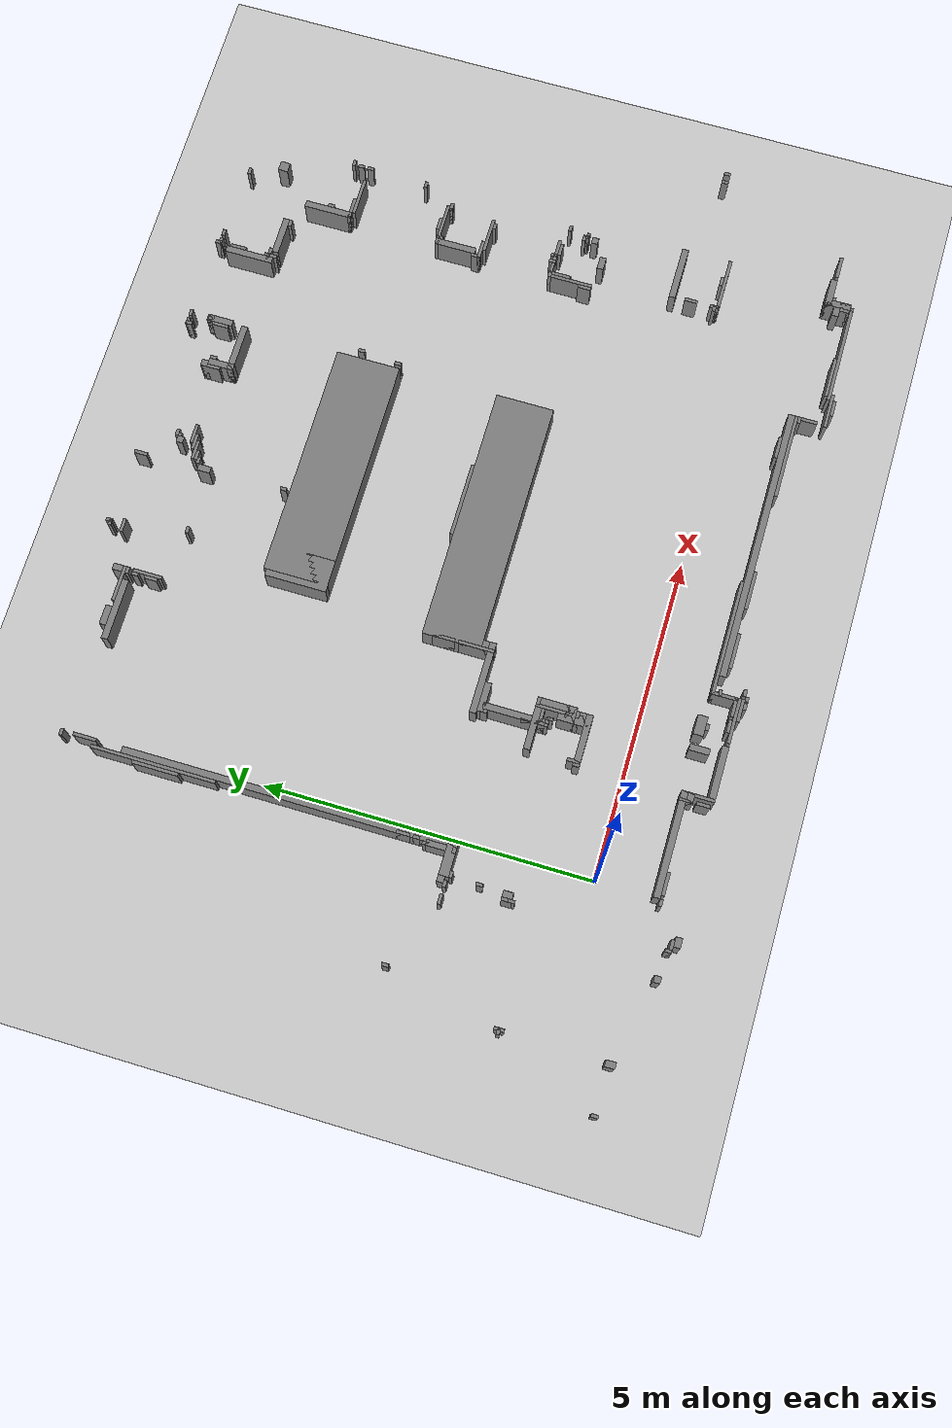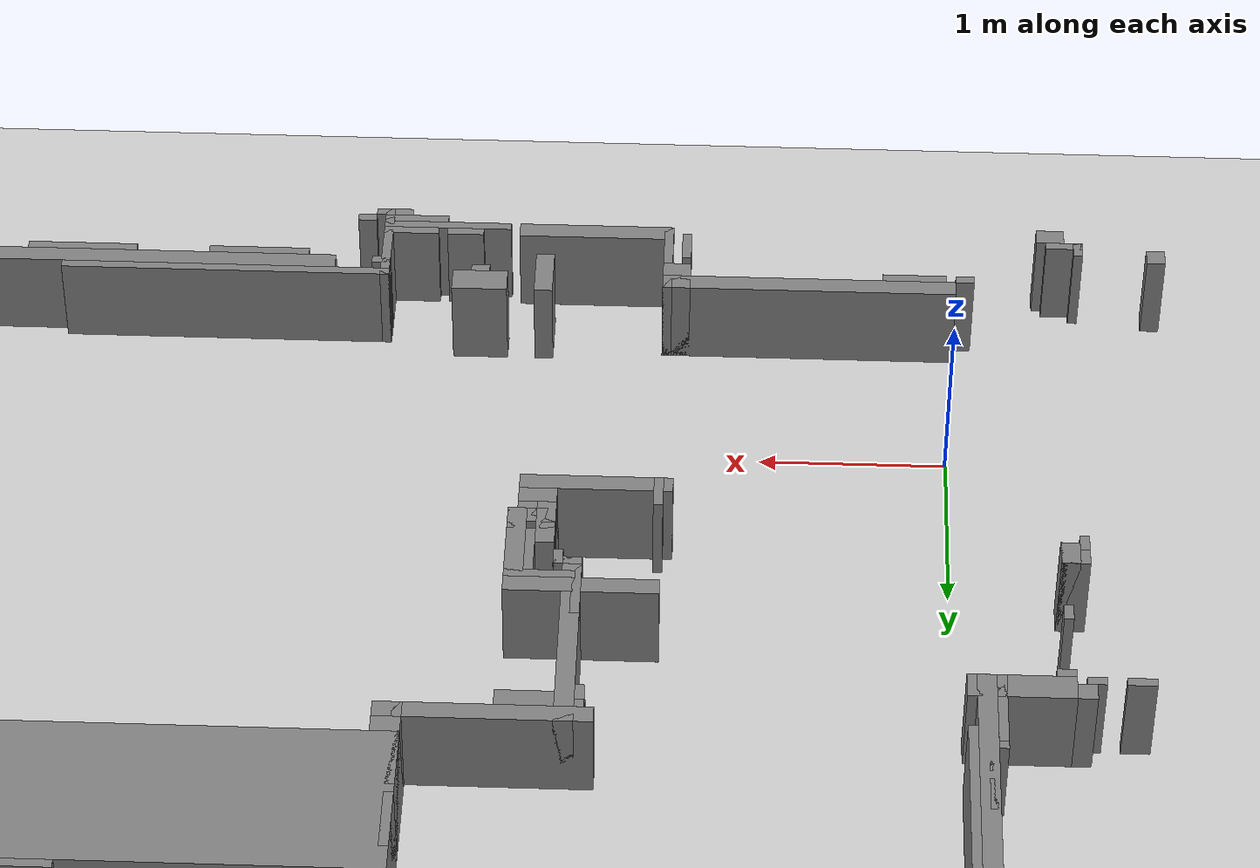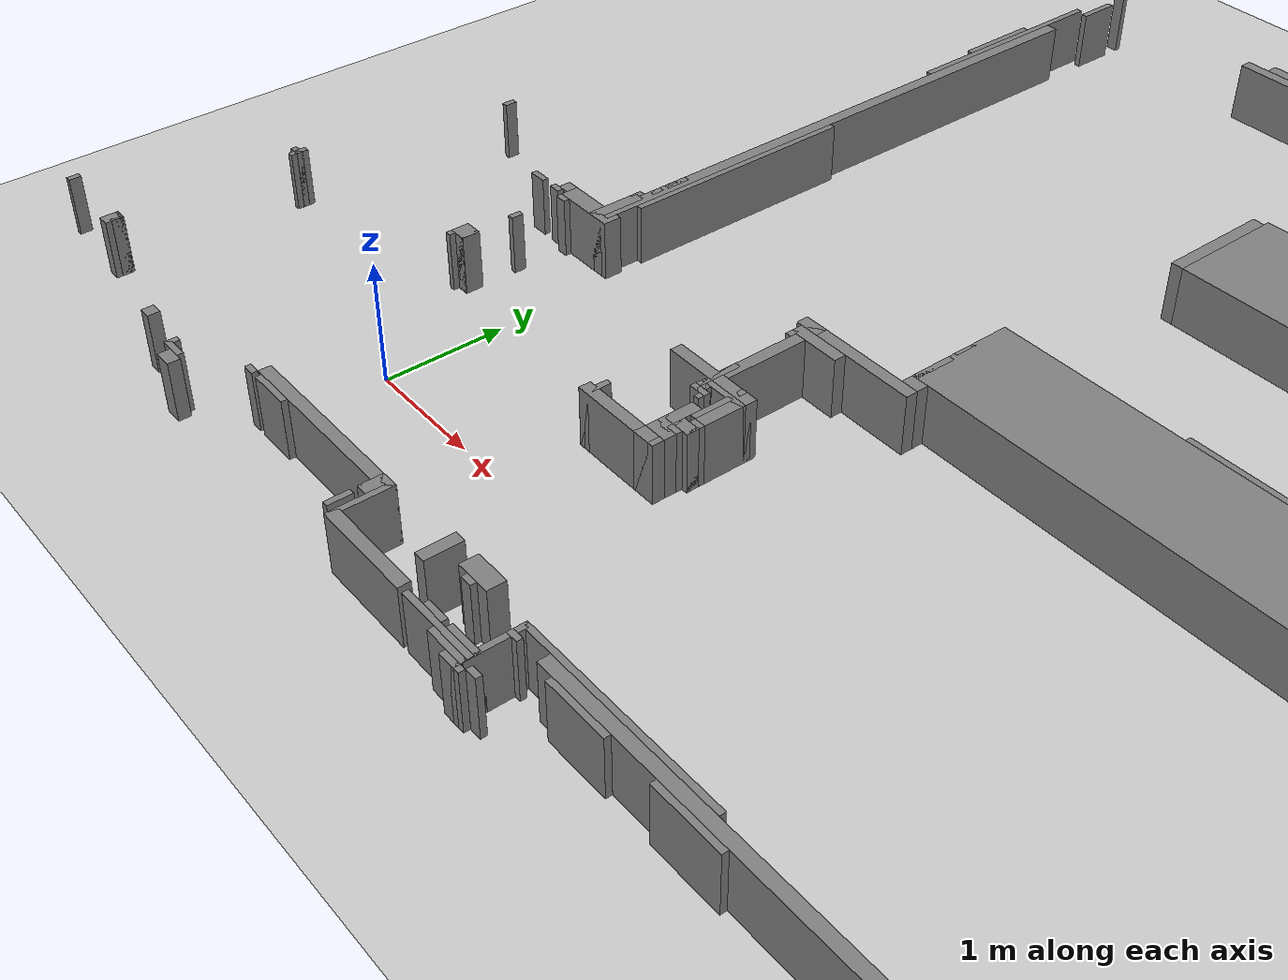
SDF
<?xml version="1.0"?>
<sdf version="1.6">
  <world name="2F_world">
    <physics type="ode">
      <max_step_size>0.001</max_step_size>
      <real_time_factor>1</real_time_factor>
    </physics>
    <include><uri>model://ground_plane</uri></include>
    <include><uri>model://sun</uri></include>

    <model name="wall_0">
      <static>true</static>
      <pose>3.1 8.385 0.25 0 0 0</pose>
      <link name="link">
        <collision name="collision">
          <geometry><box><size>0.1 0.05 0.5</size></box></geometry>
        </collision>
        <visual name="visual">
          <geometry><box><size>0.1 0.05 0.5</size></box></geometry>
          <material><ambient>0.5 0.5 0.5 1</ambient></material>
        </visual>
      </link>
    </model>

    <model name="wall_1">
      <static>true</static>
      <pose>6.55 8.335 0.25 0 0 0</pose>
      <link name="link">
        <collision name="collision">
          <geometry><box><size>0.1 0.05 0.5</size></box></geometry>
        </collision>
        <visual name="visual">
          <geometry><box><size>0.1 0.05 0.5</size></box></geometry>
          <material><ambient>0.5 0.5 0.5 1</ambient></material>
        </visual>
      </link>
    </model>

    <model name="wall_2">
      <static>true</static>
      <pose>6.7 8.335 0.25 0 0 0</pose>
      <link name="link">
        <collision name="collision">
          <geometry><box><size>0.1 0.05 0.5</size></box></geometry>
        </collision>
        <visual name="visual">
          <geometry><box><size>0.1 0.05 0.5</size></box></geometry>
          <material><ambient>0.5 0.5 0.5 1</ambient></material>
        </visual>
      </link>
    </model>

    <model name="wall_3">
      <static>true</static>
      <pose>8.0 8.285 0.25 0 0 0</pose>
      <link name="link">
        <collision name="collision">
          <geometry><box><size>0.1 0.05 0.5</size></box></geometry>
        </collision>
        <visual name="visual">
          <geometry><box><size>0.1 0.05 0.5</size></box></geometry>
          <material><ambient>0.5 0.5 0.5 1</ambient></material>
        </visual>
      </link>
    </model>

    <model name="wall_4">
      <static>true</static>
      <pose>8.15 8.285 0.25 0 0 0</pose>
      <link name="link">
        <collision name="collision">
          <geometry><box><size>0.1 0.05 0.5</size></box></geometry>
        </collision>
        <visual name="visual">
          <geometry><box><size>0.1 0.05 0.5</size></box></geometry>
          <material><ambient>0.5 0.5 0.5 1</ambient></material>
        </visual>
      </link>
    </model>

    <model name="wall_5">
      <static>true</static>
      <pose>9.3 8.235 0.25 0 0 0</pose>
      <link name="link">
        <collision name="collision">
          <geometry><box><size>0.1 0.05 0.5</size></box></geometry>
        </collision>
        <visual name="visual">
          <geometry><box><size>0.1 0.05 0.5</size></box></geometry>
          <material><ambient>0.5 0.5 0.5 1</ambient></material>
        </visual>
      </link>
    </model>

    <model name="wall_6">
      <static>true</static>
      <pose>3.1 8.185 0.25 0 0 0</pose>
      <link name="link">
        <collision name="collision">
          <geometry><box><size>0.2 0.05 0.5</size></box></geometry>
        </collision>
        <visual name="visual">
          <geometry><box><size>0.2 0.05 0.5</size></box></geometry>
          <material><ambient>0.5 0.5 0.5 1</ambient></material>
        </visual>
      </link>
    </model>

    <model name="wall_7">
      <static>true</static>
      <pose>-0.15 7.985 0.25 0 0 0</pose>
      <link name="link">
        <collision name="collision">
          <geometry><box><size>0.1 0.05 0.5</size></box></geometry>
        </collision>
        <visual name="visual">
          <geometry><box><size>0.1 0.05 0.5</size></box></geometry>
          <material><ambient>0.5 0.5 0.5 1</ambient></material>
        </visual>
      </link>
    </model>

    <model name="wall_8">
      <static>true</static>
      <pose>6.7 8.01 0.25 0 0 0</pose>
      <link name="link">
        <collision name="collision">
          <geometry><box><size>0.1 0.1 0.5</size></box></geometry>
        </collision>
        <visual name="visual">
          <geometry><box><size>0.1 0.1 0.5</size></box></geometry>
          <material><ambient>0.5 0.5 0.5 1</ambient></material>
        </visual>
      </link>
    </model>

    <model name="wall_9">
      <static>true</static>
      <pose>1.7 7.96 0.25 0 0 0</pose>
      <link name="link">
        <collision name="collision">
          <geometry><box><size>0.3 0.1 0.5</size></box></geometry>
        </collision>
        <visual name="visual">
          <geometry><box><size>0.3 0.1 0.5</size></box></geometry>
          <material><ambient>0.5 0.5 0.5 1</ambient></material>
        </visual>
      </link>
    </model>

    <model name="wall_10">
      <static>true</static>
      <pose>2.225 7.935 0.25 0 0 0</pose>
      <link name="link">
        <collision name="collision">
          <geometry><box><size>0.55 0.05 0.5</size></box></geometry>
        </collision>
        <visual name="visual">
          <geometry><box><size>0.55 0.05 0.5</size></box></geometry>
          <material><ambient>0.5 0.5 0.5 1</ambient></material>
        </visual>
      </link>
    </model>

    <model name="wall_11">
      <static>true</static>
      <pose>4.75 7.885 0.25 0 0 0</pose>
      <link name="link">
        <collision name="collision">
          <geometry><box><size>0.1 0.05 0.5</size></box></geometry>
        </collision>
        <visual name="visual">
          <geometry><box><size>0.1 0.05 0.5</size></box></geometry>
          <material><ambient>0.5 0.5 0.5 1</ambient></material>
        </visual>
      </link>
    </model>

    <model name="wall_12">
      <static>true</static>
      <pose>1.825 7.86 0.25 0 0 0</pose>
      <link name="link">
        <collision name="collision">
          <geometry><box><size>0.95 0.1 0.5</size></box></geometry>
        </collision>
        <visual name="visual">
          <geometry><box><size>0.95 0.1 0.5</size></box></geometry>
          <material><ambient>0.5 0.5 0.5 1</ambient></material>
        </visual>
      </link>
    </model>

    <model name="wall_13">
      <static>true</static>
      <pose>5.95 7.86 0.25 0 0 0</pose>
      <link name="link">
        <collision name="collision">
          <geometry><box><size>0.1 0.1 0.5</size></box></geometry>
        </collision>
        <visual name="visual">
          <geometry><box><size>0.1 0.1 0.5</size></box></geometry>
          <material><ambient>0.5 0.5 0.5 1</ambient></material>
        </visual>
      </link>
    </model>

    <model name="wall_14">
      <static>true</static>
      <pose>4.65 7.81 0.25 0 0 0</pose>
      <link name="link">
        <collision name="collision">
          <geometry><box><size>0.1 0.1 0.5</size></box></geometry>
        </collision>
        <visual name="visual">
          <geometry><box><size>0.1 0.1 0.5</size></box></geometry>
          <material><ambient>0.5 0.5 0.5 1</ambient></material>
        </visual>
      </link>
    </model>

    <model name="wall_15">
      <static>true</static>
      <pose>2.45 7.76 0.25 0 0 0</pose>
      <link name="link">
        <collision name="collision">
          <geometry><box><size>0.1 0.1 0.5</size></box></geometry>
        </collision>
        <visual name="visual">
          <geometry><box><size>0.1 0.1 0.5</size></box></geometry>
          <material><ambient>0.5 0.5 0.5 1</ambient></material>
        </visual>
      </link>
    </model>

    <model name="wall_16">
      <static>true</static>
      <pose>9.525 7.735 0.25 0 0 0</pose>
      <link name="link">
        <collision name="collision">
          <geometry><box><size>0.15 0.15 0.5</size></box></geometry>
        </collision>
        <visual name="visual">
          <geometry><box><size>0.15 0.15 0.5</size></box></geometry>
          <material><ambient>0.5 0.5 0.5 1</ambient></material>
        </visual>
      </link>
    </model>

    <model name="wall_17">
      <static>true</static>
      <pose>4.8 7.635 0.25 0 0 0</pose>
      <link name="link">
        <collision name="collision">
          <geometry><box><size>0.3 0.05 0.5</size></box></geometry>
        </collision>
        <visual name="visual">
          <geometry><box><size>0.3 0.05 0.5</size></box></geometry>
          <material><ambient>0.5 0.5 0.5 1</ambient></material>
        </visual>
      </link>
    </model>

    <model name="wall_18">
      <static>true</static>
      <pose>4.675 7.585 0.25 0 0 0</pose>
      <link name="link">
        <collision name="collision">
          <geometry><box><size>0.25 0.05 0.5</size></box></geometry>
        </collision>
        <visual name="visual">
          <geometry><box><size>0.25 0.05 0.5</size></box></geometry>
          <material><ambient>0.5 0.5 0.5 1</ambient></material>
        </visual>
      </link>
    </model>

    <model name="wall_19">
      <static>true</static>
      <pose>4.55 7.535 0.25 0 0 0</pose>
      <link name="link">
        <collision name="collision">
          <geometry><box><size>0.3 0.05 0.5</size></box></geometry>
        </collision>
        <visual name="visual">
          <geometry><box><size>0.3 0.05 0.5</size></box></geometry>
          <material><ambient>0.5 0.5 0.5 1</ambient></material>
        </visual>
      </link>
    </model>

    <model name="wall_20">
      <static>true</static>
      <pose>4.475 7.485 0.25 0 0 0</pose>
      <link name="link">
        <collision name="collision">
          <geometry><box><size>0.15 0.05 0.5</size></box></geometry>
        </collision>
        <visual name="visual">
          <geometry><box><size>0.15 0.05 0.5</size></box></geometry>
          <material><ambient>0.5 0.5 0.5 1</ambient></material>
        </visual>
      </link>
    </model>

    <model name="wall_21">
      <static>true</static>
      <pose>8.0 7.485 0.25 0 0 0</pose>
      <link name="link">
        <collision name="collision">
          <geometry><box><size>0.2 0.05 0.5</size></box></geometry>
        </collision>
        <visual name="visual">
          <geometry><box><size>0.2 0.05 0.5</size></box></geometry>
          <material><ambient>0.5 0.5 0.5 1</ambient></material>
        </visual>
      </link>
    </model>

    <model name="wall_22">
      <static>true</static>
      <pose>4.4 7.435 0.25 0 0 0</pose>
      <link name="link">
        <collision name="collision">
          <geometry><box><size>0.1 0.05 0.5</size></box></geometry>
        </collision>
        <visual name="visual">
          <geometry><box><size>0.1 0.05 0.5</size></box></geometry>
          <material><ambient>0.5 0.5 0.5 1</ambient></material>
        </visual>
      </link>
    </model>

    <model name="wall_23">
      <static>true</static>
      <pose>6.325 7.46 0.25 0 0 0</pose>
      <link name="link">
        <collision name="collision">
          <geometry><box><size>0.75 0.1 0.5</size></box></geometry>
        </collision>
        <visual name="visual">
          <geometry><box><size>0.75 0.1 0.5</size></box></geometry>
          <material><ambient>0.5 0.5 0.5 1</ambient></material>
        </visual>
      </link>
    </model>

    <model name="wall_24">
      <static>true</static>
      <pose>8.35 7.41 0.25 0 0 0</pose>
      <link name="link">
        <collision name="collision">
          <geometry><box><size>0.6 0.1 0.5</size></box></geometry>
        </collision>
        <visual name="visual">
          <geometry><box><size>0.6 0.1 0.5</size></box></geometry>
          <material><ambient>0.5 0.5 0.5 1</ambient></material>
        </visual>
      </link>
    </model>

    <model name="wall_25">
      <static>true</static>
      <pose>8.6 7.335 0.25 0 0 0</pose>
      <link name="link">
        <collision name="collision">
          <geometry><box><size>0.1 0.05 0.5</size></box></geometry>
        </collision>
        <visual name="visual">
          <geometry><box><size>0.1 0.05 0.5</size></box></geometry>
          <material><ambient>0.5 0.5 0.5 1</ambient></material>
        </visual>
      </link>
    </model>

    <model name="wall_26">
      <static>true</static>
      <pose>3.3 7.235 0.25 0 0 0</pose>
      <link name="link">
        <collision name="collision">
          <geometry><box><size>0.1 0.05 0.5</size></box></geometry>
        </collision>
        <visual name="visual">
          <geometry><box><size>0.1 0.05 0.5</size></box></geometry>
          <material><ambient>0.5 0.5 0.5 1</ambient></material>
        </visual>
      </link>
    </model>

    <model name="wall_27">
      <static>true</static>
      <pose>9.9 6.685 0.25 0 0 0</pose>
      <link name="link">
        <collision name="collision">
          <geometry><box><size>0.1 0.05 0.5</size></box></geometry>
        </collision>
        <visual name="visual">
          <geometry><box><size>0.1 0.05 0.5</size></box></geometry>
          <material><ambient>0.5 0.5 0.5 1</ambient></material>
        </visual>
      </link>
    </model>

    <model name="wall_28">
      <static>true</static>
      <pose>9.125 6.485 0.25 0 0 0</pose>
      <link name="link">
        <collision name="collision">
          <geometry><box><size>0.35 0.05 0.5</size></box></geometry>
        </collision>
        <visual name="visual">
          <geometry><box><size>0.35 0.05 0.5</size></box></geometry>
          <material><ambient>0.5 0.5 0.5 1</ambient></material>
        </visual>
      </link>
    </model>

    <model name="wall_29">
      <static>true</static>
      <pose>9.35 6.435 0.25 0 0 0</pose>
      <link name="link">
        <collision name="collision">
          <geometry><box><size>0.6 0.05 0.5</size></box></geometry>
        </collision>
        <visual name="visual">
          <geometry><box><size>0.6 0.05 0.5</size></box></geometry>
          <material><ambient>0.5 0.5 0.5 1</ambient></material>
        </visual>
      </link>
    </model>

    <model name="wall_30">
      <static>true</static>
      <pose>9.85 5.485 0.25 0 0 0</pose>
      <link name="link">
        <collision name="collision">
          <geometry><box><size>0.1 0.05 0.5</size></box></geometry>
        </collision>
        <visual name="visual">
          <geometry><box><size>0.1 0.05 0.5</size></box></geometry>
          <material><ambient>0.5 0.5 0.5 1</ambient></material>
        </visual>
      </link>
    </model>

    <model name="wall_31">
      <static>true</static>
      <pose>9.25 5.085 0.25 0 0 0</pose>
      <link name="link">
        <collision name="collision">
          <geometry><box><size>0.2 0.05 0.5</size></box></geometry>
        </collision>
        <visual name="visual">
          <geometry><box><size>0.2 0.05 0.5</size></box></geometry>
          <material><ambient>0.5 0.5 0.5 1</ambient></material>
        </visual>
      </link>
    </model>

    <model name="wall_32">
      <static>true</static>
      <pose>9.25 5.035 0.25 0 0 0</pose>
      <link name="link">
        <collision name="collision">
          <geometry><box><size>0.7 0.05 0.5</size></box></geometry>
        </collision>
        <visual name="visual">
          <geometry><box><size>0.7 0.05 0.5</size></box></geometry>
          <material><ambient>0.5 0.5 0.5 1</ambient></material>
        </visual>
      </link>
    </model>

    <model name="wall_33">
      <static>true</static>
      <pose>4.875 5.46 0.25 0 0 0</pose>
      <link name="link">
        <collision name="collision">
          <geometry><box><size>3.65 1.0 0.5</size></box></geometry>
        </collision>
        <visual name="visual">
          <geometry><box><size>3.65 1.0 0.5</size></box></geometry>
          <material><ambient>0.5 0.5 0.5 1</ambient></material>
        </visual>
      </link>
    </model>

    <model name="wall_34">
      <static>true</static>
      <pose>9.6 4.985 0.25 0 0 0</pose>
      <link name="link">
        <collision name="collision">
          <geometry><box><size>0.1 0.05 0.5</size></box></geometry>
        </collision>
        <visual name="visual">
          <geometry><box><size>0.1 0.05 0.5</size></box></geometry>
          <material><ambient>0.5 0.5 0.5 1</ambient></material>
        </visual>
      </link>
    </model>

    <model name="wall_35">
      <static>true</static>
      <pose>9.0 4.335 0.25 0 0 0</pose>
      <link name="link">
        <collision name="collision">
          <geometry><box><size>0.3 0.05 0.5</size></box></geometry>
        </collision>
        <visual name="visual">
          <geometry><box><size>0.3 0.05 0.5</size></box></geometry>
          <material><ambient>0.5 0.5 0.5 1</ambient></material>
        </visual>
      </link>
    </model>

    <model name="wall_36">
      <static>true</static>
      <pose>9.275 4.285 0.25 0 0 0</pose>
      <link name="link">
        <collision name="collision">
          <geometry><box><size>0.55 0.05 0.5</size></box></geometry>
        </collision>
        <visual name="visual">
          <geometry><box><size>0.55 0.05 0.5</size></box></geometry>
          <material><ambient>0.5 0.5 0.5 1</ambient></material>
        </visual>
      </link>
    </model>

    <model name="wall_37">
      <static>true</static>
      <pose>9.45 4.235 0.25 0 0 0</pose>
      <link name="link">
        <collision name="collision">
          <geometry><box><size>0.1 0.05 0.5</size></box></geometry>
        </collision>
        <visual name="visual">
          <geometry><box><size>0.1 0.05 0.5</size></box></geometry>
          <material><ambient>0.5 0.5 0.5 1</ambient></material>
        </visual>
      </link>
    </model>

    <model name="wall_38">
      <static>true</static>
      <pose>4.925 3.435 0.25 0 0 0</pose>
      <link name="link">
        <collision name="collision">
          <geometry><box><size>1.15 0.05 0.5</size></box></geometry>
        </collision>
        <visual name="visual">
          <geometry><box><size>1.15 0.05 0.5</size></box></geometry>
          <material><ambient>0.5 0.5 0.5 1</ambient></material>
        </visual>
      </link>
    </model>

    <model name="wall_39">
      <static>true</static>
      <pose>9.175 3.185 0.25 0 0 0</pose>
      <link name="link">
        <collision name="collision">
          <geometry><box><size>0.65 0.05 0.5</size></box></geometry>
        </collision>
        <visual name="visual">
          <geometry><box><size>0.65 0.05 0.5</size></box></geometry>
          <material><ambient>0.5 0.5 0.5 1</ambient></material>
        </visual>
      </link>
    </model>

    <model name="wall_40">
      <static>true</static>
      <pose>9.35 3.135 0.25 0 0 0</pose>
      <link name="link">
        <collision name="collision">
          <geometry><box><size>0.2 0.05 0.5</size></box></geometry>
        </collision>
        <visual name="visual">
          <geometry><box><size>0.2 0.05 0.5</size></box></geometry>
          <material><ambient>0.5 0.5 0.5 1</ambient></material>
        </visual>
      </link>
    </model>

    <model name="wall_41">
      <static>true</static>
      <pose>9.75 3.085 0.25 0 0 0</pose>
      <link name="link">
        <collision name="collision">
          <geometry><box><size>0.1 0.05 0.5</size></box></geometry>
        </collision>
        <visual name="visual">
          <geometry><box><size>0.1 0.05 0.5</size></box></geometry>
          <material><ambient>0.5 0.5 0.5 1</ambient></material>
        </visual>
      </link>
    </model>

    <model name="wall_42">
      <static>true</static>
      <pose>9.65 2.835 0.25 0 0 0</pose>
      <link name="link">
        <collision name="collision">
          <geometry><box><size>0.1 0.05 0.5</size></box></geometry>
        </collision>
        <visual name="visual">
          <geometry><box><size>0.1 0.05 0.5</size></box></geometry>
          <material><ambient>0.5 0.5 0.5 1</ambient></material>
        </visual>
      </link>
    </model>

    <model name="wall_43">
      <static>true</static>
      <pose>9.7 2.785 0.25 0 0 0</pose>
      <link name="link">
        <collision name="collision">
          <geometry><box><size>0.1 0.05 0.5</size></box></geometry>
        </collision>
        <visual name="visual">
          <geometry><box><size>0.1 0.05 0.5</size></box></geometry>
          <material><ambient>0.5 0.5 0.5 1</ambient></material>
        </visual>
      </link>
    </model>

    <model name="wall_44">
      <static>true</static>
      <pose>9.65 2.66 0.25 0 0 0</pose>
      <link name="link">
        <collision name="collision">
          <geometry><box><size>0.1 0.1 0.5</size></box></geometry>
        </collision>
        <visual name="visual">
          <geometry><box><size>0.1 0.1 0.5</size></box></geometry>
          <material><ambient>0.5 0.5 0.5 1</ambient></material>
        </visual>
      </link>
    </model>

    <model name="wall_45">
      <static>true</static>
      <pose>4.725 2.96 0.25 0 0 0</pose>
      <link name="link">
        <collision name="collision">
          <geometry><box><size>3.95 0.9 0.5</size></box></geometry>
        </collision>
        <visual name="visual">
          <geometry><box><size>3.95 0.9 0.5</size></box></geometry>
          <material><ambient>0.5 0.5 0.5 1</ambient></material>
        </visual>
      </link>
    </model>

    <model name="wall_46">
      <static>true</static>
      <pose>2.825 2.46 0.25 0 0 0</pose>
      <link name="link">
        <collision name="collision">
          <geometry><box><size>0.15 0.1 0.5</size></box></geometry>
        </collision>
        <visual name="visual">
          <geometry><box><size>0.15 0.1 0.5</size></box></geometry>
          <material><ambient>0.5 0.5 0.5 1</ambient></material>
        </visual>
      </link>
    </model>

    <model name="wall_47">
      <static>true</static>
      <pose>9.3 2.46 0.25 0 0 0</pose>
      <link name="link">
        <collision name="collision">
          <geometry><box><size>0.2 0.1 0.5</size></box></geometry>
        </collision>
        <visual name="visual">
          <geometry><box><size>0.2 0.1 0.5</size></box></geometry>
          <material><ambient>0.5 0.5 0.5 1</ambient></material>
        </visual>
      </link>
    </model>

    <model name="wall_48">
      <static>true</static>
      <pose>2.35 2.36 0.25 0 0 0</pose>
      <link name="link">
        <collision name="collision">
          <geometry><box><size>1.1 0.1 0.5</size></box></geometry>
        </collision>
        <visual name="visual">
          <geometry><box><size>1.1 0.1 0.5</size></box></geometry>
          <material><ambient>0.5 0.5 0.5 1</ambient></material>
        </visual>
      </link>
    </model>

    <model name="wall_49">
      <static>true</static>
      <pose>2.075 2.26 0.25 0 0 0</pose>
      <link name="link">
        <collision name="collision">
          <geometry><box><size>0.45 0.1 0.5</size></box></geometry>
        </collision>
        <visual name="visual">
          <geometry><box><size>0.45 0.1 0.5</size></box></geometry>
          <material><ambient>0.5 0.5 0.5 1</ambient></material>
        </visual>
      </link>
    </model>

    <model name="wall_50">
      <static>true</static>
      <pose>-0.65 2.11 0.25 0 0 0</pose>
      <link name="link">
        <collision name="collision">
          <geometry><box><size>0.1 0.1 0.5</size></box></geometry>
        </collision>
        <visual name="visual">
          <geometry><box><size>0.1 0.1 0.5</size></box></geometry>
          <material><ambient>0.5 0.5 0.5 1</ambient></material>
        </visual>
      </link>
    </model>

    <model name="wall_51">
      <static>true</static>
      <pose>-0.925 2.035 0.25 0 0 0</pose>
      <link name="link">
        <collision name="collision">
          <geometry><box><size>0.15 0.05 0.5</size></box></geometry>
        </collision>
        <visual name="visual">
          <geometry><box><size>0.15 0.05 0.5</size></box></geometry>
          <material><ambient>0.5 0.5 0.5 1</ambient></material>
        </visual>
      </link>
    </model>

    <model name="wall_52">
      <static>true</static>
      <pose>-0.7 2.035 0.25 0 0 0</pose>
      <link name="link">
        <collision name="collision">
          <geometry><box><size>0.1 0.05 0.5</size></box></geometry>
        </collision>
        <visual name="visual">
          <geometry><box><size>0.1 0.05 0.5</size></box></geometry>
          <material><ambient>0.5 0.5 0.5 1</ambient></material>
        </visual>
      </link>
    </model>

    <model name="wall_53">
      <static>true</static>
      <pose>-0.325 2.085 0.25 0 0 0</pose>
      <link name="link">
        <collision name="collision">
          <geometry><box><size>0.55 0.15 0.5</size></box></geometry>
        </collision>
        <visual name="visual">
          <geometry><box><size>0.55 0.15 0.5</size></box></geometry>
          <material><ambient>0.5 0.5 0.5 1</ambient></material>
        </visual>
      </link>
    </model>

    <model name="wall_54">
      <static>true</static>
      <pose>-0.55 1.985 0.25 0 0 0</pose>
      <link name="link">
        <collision name="collision">
          <geometry><box><size>0.1 0.05 0.5</size></box></geometry>
        </collision>
        <visual name="visual">
          <geometry><box><size>0.1 0.05 0.5</size></box></geometry>
          <material><ambient>0.5 0.5 0.5 1</ambient></material>
        </visual>
      </link>
    </model>

    <model name="wall_55">
      <static>true</static>
      <pose>1.9 1.46 0.25 0 0 0</pose>
      <link name="link">
        <collision name="collision">
          <geometry><box><size>0.8 0.1 0.5</size></box></geometry>
        </collision>
        <visual name="visual">
          <geometry><box><size>0.8 0.1 0.5</size></box></geometry>
          <material><ambient>0.5 0.5 0.5 1</ambient></material>
        </visual>
      </link>
    </model>

    <model name="wall_56">
      <static>true</static>
      <pose>2.1 1.385 0.25 0 0 0</pose>
      <link name="link">
        <collision name="collision">
          <geometry><box><size>0.4 0.05 0.5</size></box></geometry>
        </collision>
        <visual name="visual">
          <geometry><box><size>0.4 0.05 0.5</size></box></geometry>
          <material><ambient>0.5 0.5 0.5 1</ambient></material>
        </visual>
      </link>
    </model>

    <model name="wall_57">
      <static>true</static>
      <pose>1.95 1.335 0.25 0 0 0</pose>
      <link name="link">
        <collision name="collision">
          <geometry><box><size>0.1 0.05 0.5</size></box></geometry>
        </collision>
        <visual name="visual">
          <geometry><box><size>0.1 0.05 0.5</size></box></geometry>
          <material><ambient>0.5 0.5 0.5 1</ambient></material>
        </visual>
      </link>
    </model>

    <model name="wall_58">
      <static>true</static>
      <pose>2.0 1.285 0.25 0 0 0</pose>
      <link name="link">
        <collision name="collision">
          <geometry><box><size>0.1 0.05 0.5</size></box></geometry>
        </collision>
        <visual name="visual">
          <geometry><box><size>0.1 0.05 0.5</size></box></geometry>
          <material><ambient>0.5 0.5 0.5 1</ambient></material>
        </visual>
      </link>
    </model>

    <model name="wall_59">
      <static>true</static>
      <pose>9.475 1.26 0.25 0 0 0</pose>
      <link name="link">
        <collision name="collision">
          <geometry><box><size>0.85 0.1 0.5</size></box></geometry>
        </collision>
        <visual name="visual">
          <geometry><box><size>0.85 0.1 0.5</size></box></geometry>
          <material><ambient>0.5 0.5 0.5 1</ambient></material>
        </visual>
      </link>
    </model>

    <model name="wall_60">
      <static>true</static>
      <pose>-0.625 1.135 0.25 0 0 0</pose>
      <link name="link">
        <collision name="collision">
          <geometry><box><size>0.15 0.15 0.5</size></box></geometry>
        </collision>
        <visual name="visual">
          <geometry><box><size>0.15 0.15 0.5</size></box></geometry>
          <material><ambient>0.5 0.5 0.5 1</ambient></material>
        </visual>
      </link>
    </model>

    <model name="wall_61">
      <static>true</static>
      <pose>2.1 1.035 0.25 0 0 0</pose>
      <link name="link">
        <collision name="collision">
          <geometry><box><size>0.1 0.05 0.5</size></box></geometry>
        </collision>
        <visual name="visual">
          <geometry><box><size>0.1 0.05 0.5</size></box></geometry>
          <material><ambient>0.5 0.5 0.5 1</ambient></material>
        </visual>
      </link>
    </model>

    <model name="wall_62">
      <static>true</static>
      <pose>2.25 1.035 0.25 0 0 0</pose>
      <link name="link">
        <collision name="collision">
          <geometry><box><size>0.1 0.05 0.5</size></box></geometry>
        </collision>
        <visual name="visual">
          <geometry><box><size>0.1 0.05 0.5</size></box></geometry>
          <material><ambient>0.5 0.5 0.5 1</ambient></material>
        </visual>
      </link>
    </model>

    <model name="wall_63">
      <static>true</static>
      <pose>2.175 0.96 0.25 0 0 0</pose>
      <link name="link">
        <collision name="collision">
          <geometry><box><size>0.25 0.1 0.5</size></box></geometry>
        </collision>
        <visual name="visual">
          <geometry><box><size>0.25 0.1 0.5</size></box></geometry>
          <material><ambient>0.5 0.5 0.5 1</ambient></material>
        </visual>
      </link>
    </model>

    <model name="wall_64">
      <static>true</static>
      <pose>2.2 0.885 0.25 0 0 0</pose>
      <link name="link">
        <collision name="collision">
          <geometry><box><size>0.1 0.05 0.5</size></box></geometry>
        </collision>
        <visual name="visual">
          <geometry><box><size>0.1 0.05 0.5</size></box></geometry>
          <material><ambient>0.5 0.5 0.5 1</ambient></material>
        </visual>
      </link>
    </model>

    <model name="wall_65">
      <static>true</static>
      <pose>2.15 0.81 0.25 0 0 0</pose>
      <link name="link">
        <collision name="collision">
          <geometry><box><size>0.2 0.1 0.5</size></box></geometry>
        </collision>
        <visual name="visual">
          <geometry><box><size>0.2 0.1 0.5</size></box></geometry>
          <material><ambient>0.5 0.5 0.5 1</ambient></material>
        </visual>
      </link>
    </model>

    <model name="wall_66">
      <static>true</static>
      <pose>-2.45 0.735 0.25 0 0 0</pose>
      <link name="link">
        <collision name="collision">
          <geometry><box><size>0.1 0.05 0.5</size></box></geometry>
        </collision>
        <visual name="visual">
          <geometry><box><size>0.1 0.05 0.5</size></box></geometry>
          <material><ambient>0.5 0.5 0.5 1</ambient></material>
        </visual>
      </link>
    </model>

    <model name="wall_67">
      <static>true</static>
      <pose>1.85 0.71 0.25 0 0 0</pose>
      <link name="link">
        <collision name="collision">
          <geometry><box><size>0.8 0.1 0.5</size></box></geometry>
        </collision>
        <visual name="visual">
          <geometry><box><size>0.8 0.1 0.5</size></box></geometry>
          <material><ambient>0.5 0.5 0.5 1</ambient></material>
        </visual>
      </link>
    </model>

    <model name="wall_68">
      <static>true</static>
      <pose>9.05 0.585 0.25 0 0 0</pose>
      <link name="link">
        <collision name="collision">
          <geometry><box><size>0.1 0.05 0.5</size></box></geometry>
        </collision>
        <visual name="visual">
          <geometry><box><size>0.1 0.05 0.5</size></box></geometry>
          <material><ambient>0.5 0.5 0.5 1</ambient></material>
        </visual>
      </link>
    </model>

    <model name="wall_69">
      <static>true</static>
      <pose>9.525 0.585 0.25 0 0 0</pose>
      <link name="link">
        <collision name="collision">
          <geometry><box><size>0.15 0.05 0.5</size></box></geometry>
        </collision>
        <visual name="visual">
          <geometry><box><size>0.15 0.05 0.5</size></box></geometry>
          <material><ambient>0.5 0.5 0.5 1</ambient></material>
        </visual>
      </link>
    </model>

    <model name="wall_70">
      <static>true</static>
      <pose>9.475 0.535 0.25 0 0 0</pose>
      <link name="link">
        <collision name="collision">
          <geometry><box><size>0.85 0.05 0.5</size></box></geometry>
        </collision>
        <visual name="visual">
          <geometry><box><size>0.85 0.05 0.5</size></box></geometry>
          <material><ambient>0.5 0.5 0.5 1</ambient></material>
        </visual>
      </link>
    </model>

    <model name="wall_71">
      <static>true</static>
      <pose>-2.45 -0.84 0.25 0 0 0</pose>
      <link name="link">
        <collision name="collision">
          <geometry><box><size>0.1 0.1 0.5</size></box></geometry>
        </collision>
        <visual name="visual">
          <geometry><box><size>0.1 0.1 0.5</size></box></geometry>
          <material><ambient>0.5 0.5 0.5 1</ambient></material>
        </visual>
      </link>
    </model>

    <model name="wall_72">
      <static>true</static>
      <pose>0.75 -0.89 0.25 0 0 0</pose>
      <link name="link">
        <collision name="collision">
          <geometry><box><size>1.6 0.1 0.5</size></box></geometry>
        </collision>
        <visual name="visual">
          <geometry><box><size>1.6 0.1 0.5</size></box></geometry>
          <material><ambient>0.5 0.5 0.5 1</ambient></material>
        </visual>
      </link>
    </model>

    <model name="wall_73">
      <static>true</static>
      <pose>2.55 -0.865 0.25 0 0 0</pose>
      <link name="link">
        <collision name="collision">
          <geometry><box><size>0.3 0.15 0.5</size></box></geometry>
        </collision>
        <visual name="visual">
          <geometry><box><size>0.3 0.15 0.5</size></box></geometry>
          <material><ambient>0.5 0.5 0.5 1</ambient></material>
        </visual>
      </link>
    </model>

    <model name="wall_74">
      <static>true</static>
      <pose>3.95 -0.915 0.25 0 0 0</pose>
      <link name="link">
        <collision name="collision">
          <geometry><box><size>1.8 0.05 0.5</size></box></geometry>
        </collision>
        <visual name="visual">
          <geometry><box><size>1.8 0.05 0.5</size></box></geometry>
          <material><ambient>0.5 0.5 0.5 1</ambient></material>
        </visual>
      </link>
    </model>

    <model name="wall_75">
      <static>true</static>
      <pose>7.075 -0.915 0.25 0 0 0</pose>
      <link name="link">
        <collision name="collision">
          <geometry><box><size>0.35 0.05 0.5</size></box></geometry>
        </collision>
        <visual name="visual">
          <geometry><box><size>0.35 0.05 0.5</size></box></geometry>
          <material><ambient>0.5 0.5 0.5 1</ambient></material>
        </visual>
      </link>
    </model>

    <model name="wall_76">
      <static>true</static>
      <pose>-0.1 -0.965 0.25 0 0 0</pose>
      <link name="link">
        <collision name="collision">
          <geometry><box><size>0.1 0.05 0.5</size></box></geometry>
        </collision>
        <visual name="visual">
          <geometry><box><size>0.1 0.05 0.5</size></box></geometry>
          <material><ambient>0.5 0.5 0.5 1</ambient></material>
        </visual>
      </link>
    </model>

    <model name="wall_77">
      <static>true</static>
      <pose>0.175 -0.965 0.25 0 0 0</pose>
      <link name="link">
        <collision name="collision">
          <geometry><box><size>0.35 0.05 0.5</size></box></geometry>
        </collision>
        <visual name="visual">
          <geometry><box><size>0.35 0.05 0.5</size></box></geometry>
          <material><ambient>0.5 0.5 0.5 1</ambient></material>
        </visual>
      </link>
    </model>

    <model name="wall_78">
      <static>true</static>
      <pose>2.55 -0.965 0.25 0 0 0</pose>
      <link name="link">
        <collision name="collision">
          <geometry><box><size>0.1 0.05 0.5</size></box></geometry>
        </collision>
        <visual name="visual">
          <geometry><box><size>0.1 0.05 0.5</size></box></geometry>
          <material><ambient>0.5 0.5 0.5 1</ambient></material>
        </visual>
      </link>
    </model>

    <model name="wall_79">
      <static>true</static>
      <pose>1.475 -0.99 0.25 0 0 0</pose>
      <link name="link">
        <collision name="collision">
          <geometry><box><size>0.15 0.1 0.5</size></box></geometry>
        </collision>
        <visual name="visual">
          <geometry><box><size>0.15 0.1 0.5</size></box></geometry>
          <material><ambient>0.5 0.5 0.5 1</ambient></material>
        </visual>
      </link>
    </model>

    <model name="wall_80">
      <static>true</static>
      <pose>3.1 -1.015 0.25 0 0 0</pose>
      <link name="link">
        <collision name="collision">
          <geometry><box><size>0.1 0.05 0.5</size></box></geometry>
        </collision>
        <visual name="visual">
          <geometry><box><size>0.1 0.05 0.5</size></box></geometry>
          <material><ambient>0.5 0.5 0.5 1</ambient></material>
        </visual>
      </link>
    </model>

    <model name="wall_81">
      <static>true</static>
      <pose>5.5 -0.99 0.25 0 0 0</pose>
      <link name="link">
        <collision name="collision">
          <geometry><box><size>4.3 0.1 0.5</size></box></geometry>
        </collision>
        <visual name="visual">
          <geometry><box><size>4.3 0.1 0.5</size></box></geometry>
          <material><ambient>0.5 0.5 0.5 1</ambient></material>
        </visual>
      </link>
    </model>

    <model name="wall_82">
      <static>true</static>
      <pose>3.775 -1.065 0.25 0 0 0</pose>
      <link name="link">
        <collision name="collision">
          <geometry><box><size>0.55 0.05 0.5</size></box></geometry>
        </collision>
        <visual name="visual">
          <geometry><box><size>0.55 0.05 0.5</size></box></geometry>
          <material><ambient>0.5 0.5 0.5 1</ambient></material>
        </visual>
      </link>
    </model>

    <model name="wall_83">
      <static>true</static>
      <pose>4.75 -1.065 0.25 0 0 0</pose>
      <link name="link">
        <collision name="collision">
          <geometry><box><size>0.6 0.05 0.5</size></box></geometry>
        </collision>
        <visual name="visual">
          <geometry><box><size>0.6 0.05 0.5</size></box></geometry>
          <material><ambient>0.5 0.5 0.5 1</ambient></material>
        </visual>
      </link>
    </model>

    <model name="wall_84">
      <static>true</static>
      <pose>6.975 -1.065 0.25 0 0 0</pose>
      <link name="link">
        <collision name="collision">
          <geometry><box><size>1.35 0.05 0.5</size></box></geometry>
        </collision>
        <visual name="visual">
          <geometry><box><size>1.35 0.05 0.5</size></box></geometry>
          <material><ambient>0.5 0.5 0.5 1</ambient></material>
        </visual>
      </link>
    </model>

    <model name="wall_85">
      <static>true</static>
      <pose>7.6 -1.115 0.25 0 0 0</pose>
      <link name="link">
        <collision name="collision">
          <geometry><box><size>0.1 0.05 0.5</size></box></geometry>
        </collision>
        <visual name="visual">
          <geometry><box><size>0.1 0.05 0.5</size></box></geometry>
          <material><ambient>0.5 0.5 0.5 1</ambient></material>
        </visual>
      </link>
    </model>

    <model name="wall_86">
      <static>true</static>
      <pose>9.825 -1.09 0.25 0 0 0</pose>
      <link name="link">
        <collision name="collision">
          <geometry><box><size>0.45 0.1 0.5</size></box></geometry>
        </collision>
        <visual name="visual">
          <geometry><box><size>0.45 0.1 0.5</size></box></geometry>
          <material><ambient>0.5 0.5 0.5 1</ambient></material>
        </visual>
      </link>
    </model>

    <model name="wall_87">
      <static>true</static>
      <pose>10.275 -1.115 0.25 0 0 0</pose>
      <link name="link">
        <collision name="collision">
          <geometry><box><size>0.35 0.05 0.5</size></box></geometry>
        </collision>
        <visual name="visual">
          <geometry><box><size>0.35 0.05 0.5</size></box></geometry>
          <material><ambient>0.5 0.5 0.5 1</ambient></material>
        </visual>
      </link>
    </model>

    <model name="wall_88">
      <static>true</static>
      <pose>9.675 -1.165 0.25 0 0 0</pose>
      <link name="link">
        <collision name="collision">
          <geometry><box><size>0.15 0.05 0.5</size></box></geometry>
        </collision>
        <visual name="visual">
          <geometry><box><size>0.15 0.05 0.5</size></box></geometry>
          <material><ambient>0.5 0.5 0.5 1</ambient></material>
        </visual>
      </link>
    </model>

    <model name="wall_89">
      <static>true</static>
      <pose>-1.15 -1.19 0.25 0 0 0</pose>
      <link name="link">
        <collision name="collision">
          <geometry><box><size>0.1 0.1 0.5</size></box></geometry>
        </collision>
        <visual name="visual">
          <geometry><box><size>0.1 0.1 0.5</size></box></geometry>
          <material><ambient>0.5 0.5 0.5 1</ambient></material>
        </visual>
      </link>
    </model>

    <model name="wall_90">
      <static>true</static>
      <pose>-0.65 -1.265 0.25 0 0 0</pose>
      <link name="link">
        <collision name="collision">
          <geometry><box><size>0.2 0.05 0.5</size></box></geometry>
        </collision>
        <visual name="visual">
          <geometry><box><size>0.2 0.05 0.5</size></box></geometry>
          <material><ambient>0.5 0.5 0.5 1</ambient></material>
        </visual>
      </link>
    </model>

    <model name="wall_91">
      <static>true</static>
      <pose>2.65 -1.265 0.25 0 0 0</pose>
      <link name="link">
        <collision name="collision">
          <geometry><box><size>0.2 0.05 0.5</size></box></geometry>
        </collision>
        <visual name="visual">
          <geometry><box><size>0.2 0.05 0.5</size></box></geometry>
          <material><ambient>0.5 0.5 0.5 1</ambient></material>
        </visual>
      </link>
    </model>

    <model name="wall_92">
      <static>true</static>
      <pose>2.95 -1.265 0.25 0 0 0</pose>
      <link name="link">
        <collision name="collision">
          <geometry><box><size>0.3 0.05 0.5</size></box></geometry>
        </collision>
        <visual name="visual">
          <geometry><box><size>0.3 0.05 0.5</size></box></geometry>
          <material><ambient>0.5 0.5 0.5 1</ambient></material>
        </visual>
      </link>
    </model>

    <model name="wall_93">
      <static>true</static>
      <pose>9.575 -1.24 0.25 0 0 0</pose>
      <link name="link">
        <collision name="collision">
          <geometry><box><size>0.25 0.1 0.5</size></box></geometry>
        </collision>
        <visual name="visual">
          <geometry><box><size>0.25 0.1 0.5</size></box></geometry>
          <material><ambient>0.5 0.5 0.5 1</ambient></material>
        </visual>
      </link>
    </model>

    <model name="wall_94">
      <static>true</static>
      <pose>1.925 -1.29 0.25 0 0 0</pose>
      <link name="link">
        <collision name="collision">
          <geometry><box><size>0.85 0.1 0.5</size></box></geometry>
        </collision>
        <visual name="visual">
          <geometry><box><size>0.85 0.1 0.5</size></box></geometry>
          <material><ambient>0.5 0.5 0.5 1</ambient></material>
        </visual>
      </link>
    </model>

    <model name="wall_95">
      <static>true</static>
      <pose>2.75 -1.315 0.25 0 0 0</pose>
      <link name="link">
        <collision name="collision">
          <geometry><box><size>0.7 0.05 0.5</size></box></geometry>
        </collision>
        <visual name="visual">
          <geometry><box><size>0.7 0.05 0.5</size></box></geometry>
          <material><ambient>0.5 0.5 0.5 1</ambient></material>
        </visual>
      </link>
    </model>

    <model name="wall_96">
      <static>true</static>
      <pose>-0.575 -1.34 0.25 0 0 0</pose>
      <link name="link">
        <collision name="collision">
          <geometry><box><size>0.15 0.1 0.5</size></box></geometry>
        </collision>
        <visual name="visual">
          <geometry><box><size>0.15 0.1 0.5</size></box></geometry>
          <material><ambient>0.5 0.5 0.5 1</ambient></material>
        </visual>
      </link>
    </model>

    <model name="wall_97">
      <static>true</static>
      <pose>2.925 -1.365 0.25 0 0 0</pose>
      <link name="link">
        <collision name="collision">
          <geometry><box><size>0.35 0.05 0.5</size></box></geometry>
        </collision>
        <visual name="visual">
          <geometry><box><size>0.35 0.05 0.5</size></box></geometry>
          <material><ambient>0.5 0.5 0.5 1</ambient></material>
        </visual>
      </link>
    </model>

    <model name="wall_98">
      <static>true</static>
      <pose>3.2 -1.365 0.25 0 0 0</pose>
      <link name="link">
        <collision name="collision">
          <geometry><box><size>0.1 0.05 0.5</size></box></geometry>
        </collision>
        <visual name="visual">
          <geometry><box><size>0.1 0.05 0.5</size></box></geometry>
          <material><ambient>0.5 0.5 0.5 1</ambient></material>
        </visual>
      </link>
    </model>

    <model name="wall_99">
      <static>true</static>
      <pose>3.05 -1.415 0.25 0 0 0</pose>
      <link name="link">
        <collision name="collision">
          <geometry><box><size>0.2 0.05 0.5</size></box></geometry>
        </collision>
        <visual name="visual">
          <geometry><box><size>0.2 0.05 0.5</size></box></geometry>
          <material><ambient>0.5 0.5 0.5 1</ambient></material>
        </visual>
      </link>
    </model>

    <model name="wall_100">
      <static>true</static>
      <pose>8.425 -1.415 0.25 0 0 0</pose>
      <link name="link">
        <collision name="collision">
          <geometry><box><size>0.65 0.05 0.5</size></box></geometry>
        </collision>
        <visual name="visual">
          <geometry><box><size>0.65 0.05 0.5</size></box></geometry>
          <material><ambient>0.5 0.5 0.5 1</ambient></material>
        </visual>
      </link>
    </model>

    <model name="wall_101">
      <static>true</static>
      <pose>9.625 -1.365 0.25 0 0 0</pose>
      <link name="link">
        <collision name="collision">
          <geometry><box><size>0.15 0.15 0.5</size></box></geometry>
        </collision>
        <visual name="visual">
          <geometry><box><size>0.15 0.15 0.5</size></box></geometry>
          <material><ambient>0.5 0.5 0.5 1</ambient></material>
        </visual>
      </link>
    </model>

    <model name="wall_102">
      <static>true</static>
      <pose>8.85 -1.465 0.25 0 0 0</pose>
      <link name="link">
        <collision name="collision">
          <geometry><box><size>1.6 0.05 0.5</size></box></geometry>
        </collision>
        <visual name="visual">
          <geometry><box><size>1.6 0.05 0.5</size></box></geometry>
          <material><ambient>0.5 0.5 0.5 1</ambient></material>
        </visual>
      </link>
    </model>

    <model name="wall_103">
      <static>true</static>
      <pose>7.875 -1.515 0.25 0 0 0</pose>
      <link name="link">
        <collision name="collision">
          <geometry><box><size>0.55 0.05 0.5</size></box></geometry>
        </collision>
        <visual name="visual">
          <geometry><box><size>0.55 0.05 0.5</size></box></geometry>
          <material><ambient>0.5 0.5 0.5 1</ambient></material>
        </visual>
      </link>
    </model>

    <model name="wall_104">
      <static>true</static>
      <pose>7.925 -1.565 0.25 0 0 0</pose>
      <link name="link">
        <collision name="collision">
          <geometry><box><size>0.25 0.05 0.5</size></box></geometry>
        </collision>
        <visual name="visual">
          <geometry><box><size>0.25 0.05 0.5</size></box></geometry>
          <material><ambient>0.5 0.5 0.5 1</ambient></material>
        </visual>
      </link>
    </model>

    <model name="wall_105">
      <static>true</static>
      <pose>-3.175 -0.84 0.25 0 0 0</pose>
      <link name="link">
        <collision name="collision">
          <geometry><box><size>0.05 0.1 0.5</size></box></geometry>
        </collision>
        <visual name="visual">
          <geometry><box><size>0.05 0.1 0.5</size></box></geometry>
          <material><ambient>0.5 0.5 0.5 1</ambient></material>
        </visual>
      </link>
    </model>

    <model name="wall_106">
      <static>true</static>
      <pose>-2.425 0.735 0.25 0 0 0</pose>
      <link name="link">
        <collision name="collision">
          <geometry><box><size>0.05 0.15 0.5</size></box></geometry>
        </collision>
        <visual name="visual">
          <geometry><box><size>0.05 0.15 0.5</size></box></geometry>
          <material><ambient>0.5 0.5 0.5 1</ambient></material>
        </visual>
      </link>
    </model>

    <model name="wall_107">
      <static>true</static>
      <pose>-2.45 -0.865 0.25 0 0 0</pose>
      <link name="link">
        <collision name="collision">
          <geometry><box><size>0.1 0.15 0.5</size></box></geometry>
        </collision>
        <visual name="visual">
          <geometry><box><size>0.1 0.15 0.5</size></box></geometry>
          <material><ambient>0.5 0.5 0.5 1</ambient></material>
        </visual>
      </link>
    </model>

    <model name="wall_108">
      <static>true</static>
      <pose>-2.025 2.51 0.25 0 0 0</pose>
      <link name="link">
        <collision name="collision">
          <geometry><box><size>0.05 0.1 0.5</size></box></geometry>
        </collision>
        <visual name="visual">
          <geometry><box><size>0.05 0.1 0.5</size></box></geometry>
          <material><ambient>0.5 0.5 0.5 1</ambient></material>
        </visual>
      </link>
    </model>

    <model name="wall_109">
      <static>true</static>
      <pose>-0.725 -1.24 0.25 0 0 0</pose>
      <link name="link">
        <collision name="collision">
          <geometry><box><size>0.05 0.1 0.5</size></box></geometry>
        </collision>
        <visual name="visual">
          <geometry><box><size>0.05 0.1 0.5</size></box></geometry>
          <material><ambient>0.5 0.5 0.5 1</ambient></material>
        </visual>
      </link>
    </model>

    <model name="wall_110">
      <static>true</static>
      <pose>-0.675 1.06 0.25 0 0 0</pose>
      <link name="link">
        <collision name="collision">
          <geometry><box><size>0.05 0.1 0.5</size></box></geometry>
        </collision>
        <visual name="visual">
          <geometry><box><size>0.05 0.1 0.5</size></box></geometry>
          <material><ambient>0.5 0.5 0.5 1</ambient></material>
        </visual>
      </link>
    </model>

    <model name="wall_111">
      <static>true</static>
      <pose>-0.575 1.56 0.25 0 0 0</pose>
      <link name="link">
        <collision name="collision">
          <geometry><box><size>0.05 0.1 0.5</size></box></geometry>
        </collision>
        <visual name="visual">
          <geometry><box><size>0.05 0.1 0.5</size></box></geometry>
          <material><ambient>0.5 0.5 0.5 1</ambient></material>
        </visual>
      </link>
    </model>

    <model name="wall_112">
      <static>true</static>
      <pose>-0.6 1.135 0.25 0 0 0</pose>
      <link name="link">
        <collision name="collision">
          <geometry><box><size>0.1 0.15 0.5</size></box></geometry>
        </collision>
        <visual name="visual">
          <geometry><box><size>0.1 0.15 0.5</size></box></geometry>
          <material><ambient>0.5 0.5 0.5 1</ambient></material>
        </visual>
      </link>
    </model>

    <model name="wall_113">
      <static>true</static>
      <pose>-0.275 6.51 0.25 0 0 0</pose>
      <link name="link">
        <collision name="collision">
          <geometry><box><size>0.05 0.7 0.5</size></box></geometry>
        </collision>
        <visual name="visual">
          <geometry><box><size>0.05 0.7 0.5</size></box></geometry>
          <material><ambient>0.5 0.5 0.5 1</ambient></material>
        </visual>
      </link>
    </model>

    <model name="wall_114">
      <static>true</static>
      <pose>-0.225 6.56 0.25 0 0 0</pose>
      <link name="link">
        <collision name="collision">
          <geometry><box><size>0.05 1.9 0.5</size></box></geometry>
        </collision>
        <visual name="visual">
          <geometry><box><size>0.05 1.9 0.5</size></box></geometry>
          <material><ambient>0.5 0.5 0.5 1</ambient></material>
        </visual>
      </link>
    </model>

    <model name="wall_115">
      <static>true</static>
      <pose>-0.225 2.46 0.25 0 0 0</pose>
      <link name="link">
        <collision name="collision">
          <geometry><box><size>0.05 0.1 0.5</size></box></geometry>
        </collision>
        <visual name="visual">
          <geometry><box><size>0.05 0.1 0.5</size></box></geometry>
          <material><ambient>0.5 0.5 0.5 1</ambient></material>
        </visual>
      </link>
    </model>

    <model name="wall_116">
      <static>true</static>
      <pose>-0.175 2.81 0.25 0 0 0</pose>
      <link name="link">
        <collision name="collision">
          <geometry><box><size>0.05 0.2 0.5</size></box></geometry>
        </collision>
        <visual name="visual">
          <geometry><box><size>0.05 0.2 0.5</size></box></geometry>
          <material><ambient>0.5 0.5 0.5 1</ambient></material>
        </visual>
      </link>
    </model>

    <model name="wall_117">
      <static>true</static>
      <pose>-0.175 2.61 0.25 0 0 0</pose>
      <link name="link">
        <collision name="collision">
          <geometry><box><size>0.05 0.1 0.5</size></box></geometry>
        </collision>
        <visual name="visual">
          <geometry><box><size>0.05 0.1 0.5</size></box></geometry>
          <material><ambient>0.5 0.5 0.5 1</ambient></material>
        </visual>
      </link>
    </model>

    <model name="wall_118">
      <static>true</static>
      <pose>-0.2 2.235 0.25 0 0 0</pose>
      <link name="link">
        <collision name="collision">
          <geometry><box><size>0.1 0.45 0.5</size></box></geometry>
        </collision>
        <visual name="visual">
          <geometry><box><size>0.1 0.45 0.5</size></box></geometry>
          <material><ambient>0.5 0.5 0.5 1</ambient></material>
        </visual>
      </link>
    </model>

    <model name="wall_119">
      <static>true</static>
      <pose>-0.125 7.635 0.25 0 0 0</pose>
      <link name="link">
        <collision name="collision">
          <geometry><box><size>0.05 0.35 0.5</size></box></geometry>
        </collision>
        <visual name="visual">
          <geometry><box><size>0.05 0.35 0.5</size></box></geometry>
          <material><ambient>0.5 0.5 0.5 1</ambient></material>
        </visual>
      </link>
    </model>

    <model name="wall_120">
      <static>true</static>
      <pose>-0.15 4.535 0.25 0 0 0</pose>
      <link name="link">
        <collision name="collision">
          <geometry><box><size>0.1 5.05 0.5</size></box></geometry>
        </collision>
        <visual name="visual">
          <geometry><box><size>0.1 5.05 0.5</size></box></geometry>
          <material><ambient>0.5 0.5 0.5 1</ambient></material>
        </visual>
      </link>
    </model>

    <model name="wall_121">
      <static>true</static>
      <pose>-0.075 3.36 0.25 0 0 0</pose>
      <link name="link">
        <collision name="collision">
          <geometry><box><size>0.05 2.0 0.5</size></box></geometry>
        </collision>
        <visual name="visual">
          <geometry><box><size>0.05 2.0 0.5</size></box></geometry>
          <material><ambient>0.5 0.5 0.5 1</ambient></material>
        </visual>
      </link>
    </model>

    <model name="wall_122">
      <static>true</static>
      <pose>1.425 -1.19 0.25 0 0 0</pose>
      <link name="link">
        <collision name="collision">
          <geometry><box><size>0.05 0.2 0.5</size></box></geometry>
        </collision>
        <visual name="visual">
          <geometry><box><size>0.05 0.2 0.5</size></box></geometry>
          <material><ambient>0.5 0.5 0.5 1</ambient></material>
        </visual>
      </link>
    </model>

    <model name="wall_123">
      <static>true</static>
      <pose>1.475 0.71 0.25 0 0 0</pose>
      <link name="link">
        <collision name="collision">
          <geometry><box><size>0.05 0.1 0.5</size></box></geometry>
        </collision>
        <visual name="visual">
          <geometry><box><size>0.05 0.1 0.5</size></box></geometry>
          <material><ambient>0.5 0.5 0.5 1</ambient></material>
        </visual>
      </link>
    </model>

    <model name="wall_124">
      <static>true</static>
      <pose>1.45 -0.94 0.25 0 0 0</pose>
      <link name="link">
        <collision name="collision">
          <geometry><box><size>0.1 0.2 0.5</size></box></geometry>
        </collision>
        <visual name="visual">
          <geometry><box><size>0.1 0.2 0.5</size></box></geometry>
          <material><ambient>0.5 0.5 0.5 1</ambient></material>
        </visual>
      </link>
    </model>

    <model name="wall_125">
      <static>true</static>
      <pose>1.525 0.76 0.25 0 0 0</pose>
      <link name="link">
        <collision name="collision">
          <geometry><box><size>0.05 0.2 0.5</size></box></geometry>
        </collision>
        <visual name="visual">
          <geometry><box><size>0.05 0.2 0.5</size></box></geometry>
          <material><ambient>0.5 0.5 0.5 1</ambient></material>
        </visual>
      </link>
    </model>

    <model name="wall_126">
      <static>true</static>
      <pose>1.525 -1.09 0.25 0 0 0</pose>
      <link name="link">
        <collision name="collision">
          <geometry><box><size>0.05 0.5 0.5</size></box></geometry>
        </collision>
        <visual name="visual">
          <geometry><box><size>0.05 0.5 0.5</size></box></geometry>
          <material><ambient>0.5 0.5 0.5 1</ambient></material>
        </visual>
      </link>
    </model>

    <model name="wall_127">
      <static>true</static>
      <pose>1.875 2.21 0.25 0 0 0</pose>
      <link name="link">
        <collision name="collision">
          <geometry><box><size>0.05 0.1 0.5</size></box></geometry>
        </collision>
        <visual name="visual">
          <geometry><box><size>0.05 0.1 0.5</size></box></geometry>
          <material><ambient>0.5 0.5 0.5 1</ambient></material>
        </visual>
      </link>
    </model>

    <model name="wall_128">
      <static>true</static>
      <pose>1.925 1.485 0.25 0 0 0</pose>
      <link name="link">
        <collision name="collision">
          <geometry><box><size>0.05 0.35 0.5</size></box></geometry>
        </collision>
        <visual name="visual">
          <geometry><box><size>0.05 0.35 0.5</size></box></geometry>
          <material><ambient>0.5 0.5 0.5 1</ambient></material>
        </visual>
      </link>
    </model>

    <model name="wall_129">
      <static>true</static>
      <pose>1.95 1.835 0.25 0 0 0</pose>
      <link name="link">
        <collision name="collision">
          <geometry><box><size>0.1 1.15 0.5</size></box></geometry>
        </collision>
        <visual name="visual">
          <geometry><box><size>0.1 1.15 0.5</size></box></geometry>
          <material><ambient>0.5 0.5 0.5 1</ambient></material>
        </visual>
      </link>
    </model>

    <model name="wall_130">
      <static>true</static>
      <pose>2.025 1.26 0.25 0 0 0</pose>
      <link name="link">
        <collision name="collision">
          <geometry><box><size>0.05 0.1 0.5</size></box></geometry>
        </collision>
        <visual name="visual">
          <geometry><box><size>0.05 0.1 0.5</size></box></geometry>
          <material><ambient>0.5 0.5 0.5 1</ambient></material>
        </visual>
      </link>
    </model>

    <model name="wall_131">
      <static>true</static>
      <pose>2.1 1.035 0.25 0 0 0</pose>
      <link name="link">
        <collision name="collision">
          <geometry><box><size>0.1 0.25 0.5</size></box></geometry>
        </collision>
        <visual name="visual">
          <geometry><box><size>0.1 0.25 0.5</size></box></geometry>
          <material><ambient>0.5 0.5 0.5 1</ambient></material>
        </visual>
      </link>
    </model>

    <model name="wall_132">
      <static>true</static>
      <pose>2.175 1.285 0.25 0 0 0</pose>
      <link name="link">
        <collision name="collision">
          <geometry><box><size>0.05 0.45 0.5</size></box></geometry>
        </collision>
        <visual name="visual">
          <geometry><box><size>0.05 0.45 0.5</size></box></geometry>
          <material><ambient>0.5 0.5 0.5 1</ambient></material>
        </visual>
      </link>
    </model>

    <model name="wall_133">
      <static>true</static>
      <pose>2.125 0.835 0.25 0 0 0</pose>
      <link name="link">
        <collision name="collision">
          <geometry><box><size>0.15 0.35 0.5</size></box></geometry>
        </collision>
        <visual name="visual">
          <geometry><box><size>0.15 0.35 0.5</size></box></geometry>
          <material><ambient>0.5 0.5 0.5 1</ambient></material>
        </visual>
      </link>
    </model>

    <model name="wall_134">
      <static>true</static>
      <pose>2.2 -0.94 0.25 0 0 0</pose>
      <link name="link">
        <collision name="collision">
          <geometry><box><size>0.1 0.3 0.5</size></box></geometry>
        </collision>
        <visual name="visual">
          <geometry><box><size>0.1 0.3 0.5</size></box></geometry>
          <material><ambient>0.5 0.5 0.5 1</ambient></material>
        </visual>
      </link>
    </model>

    <model name="wall_135">
      <static>true</static>
      <pose>2.25 1.185 0.25 0 0 0</pose>
      <link name="link">
        <collision name="collision">
          <geometry><box><size>0.1 0.55 0.5</size></box></geometry>
        </collision>
        <visual name="visual">
          <geometry><box><size>0.1 0.55 0.5</size></box></geometry>
          <material><ambient>0.5 0.5 0.5 1</ambient></material>
        </visual>
      </link>
    </model>

    <model name="wall_136">
      <static>true</static>
      <pose>2.425 7.51 0.25 0 0 0</pose>
      <link name="link">
        <collision name="collision">
          <geometry><box><size>0.05 0.2 0.5</size></box></geometry>
        </collision>
        <visual name="visual">
          <geometry><box><size>0.05 0.2 0.5</size></box></geometry>
          <material><ambient>0.5 0.5 0.5 1</ambient></material>
        </visual>
      </link>
    </model>

    <model name="wall_137">
      <static>true</static>
      <pose>2.45 7.985 0.25 0 0 0</pose>
      <link name="link">
        <collision name="collision">
          <geometry><box><size>0.1 0.25 0.5</size></box></geometry>
        </collision>
        <visual name="visual">
          <geometry><box><size>0.1 0.25 0.5</size></box></geometry>
          <material><ambient>0.5 0.5 0.5 1</ambient></material>
        </visual>
      </link>
    </model>

    <model name="wall_138">
      <static>true</static>
      <pose>2.475 7.585 0.25 0 0 0</pose>
      <link name="link">
        <collision name="collision">
          <geometry><box><size>0.05 0.45 0.5</size></box></geometry>
        </collision>
        <visual name="visual">
          <geometry><box><size>0.05 0.45 0.5</size></box></geometry>
          <material><ambient>0.5 0.5 0.5 1</ambient></material>
        </visual>
      </link>
    </model>

    <model name="wall_139">
      <static>true</static>
      <pose>2.775 3.085 0.25 0 0 0</pose>
      <link name="link">
        <collision name="collision">
          <geometry><box><size>0.05 0.35 0.5</size></box></geometry>
        </collision>
        <visual name="visual">
          <geometry><box><size>0.05 0.35 0.5</size></box></geometry>
          <material><ambient>0.5 0.5 0.5 1</ambient></material>
        </visual>
      </link>
    </model>

    <model name="wall_140">
      <static>true</static>
      <pose>2.775 2.585 0.25 0 0 0</pose>
      <link name="link">
        <collision name="collision">
          <geometry><box><size>0.05 0.55 0.5</size></box></geometry>
        </collision>
        <visual name="visual">
          <geometry><box><size>0.05 0.55 0.5</size></box></geometry>
          <material><ambient>0.5 0.5 0.5 1</ambient></material>
        </visual>
      </link>
    </model>

    <model name="wall_141">
      <static>true</static>
      <pose>3.075 -1.165 0.25 0 0 0</pose>
      <link name="link">
        <collision name="collision">
          <geometry><box><size>0.05 0.55 0.5</size></box></geometry>
        </collision>
        <visual name="visual">
          <geometry><box><size>0.05 0.55 0.5</size></box></geometry>
          <material><ambient>0.5 0.5 0.5 1</ambient></material>
        </visual>
      </link>
    </model>

    <model name="wall_142">
      <static>true</static>
      <pose>3.125 8.41 0.25 0 0 0</pose>
      <link name="link">
        <collision name="collision">
          <geometry><box><size>0.05 0.1 0.5</size></box></geometry>
        </collision>
        <visual name="visual">
          <geometry><box><size>0.05 0.1 0.5</size></box></geometry>
          <material><ambient>0.5 0.5 0.5 1</ambient></material>
        </visual>
      </link>
    </model>

    <model name="wall_143">
      <static>true</static>
      <pose>3.2 5.435 0.25 0 0 0</pose>
      <link name="link">
        <collision name="collision">
          <geometry><box><size>0.5 0.95 0.5</size></box></geometry>
        </collision>
        <visual name="visual">
          <geometry><box><size>0.5 0.95 0.5</size></box></geometry>
          <material><ambient>0.5 0.5 0.5 1</ambient></material>
        </visual>
      </link>
    </model>

    <model name="wall_144">
      <static>true</static>
      <pose>4.275 8.31 0.25 0 0 0</pose>
      <link name="link">
        <collision name="collision">
          <geometry><box><size>0.05 0.2 0.5</size></box></geometry>
        </collision>
        <visual name="visual">
          <geometry><box><size>0.05 0.2 0.5</size></box></geometry>
          <material><ambient>0.5 0.5 0.5 1</ambient></material>
        </visual>
      </link>
    </model>

    <model name="wall_145">
      <static>true</static>
      <pose>4.3 7.31 0.25 0 0 0</pose>
      <link name="link">
        <collision name="collision">
          <geometry><box><size>0.1 0.2 0.5</size></box></geometry>
        </collision>
        <visual name="visual">
          <geometry><box><size>0.1 0.2 0.5</size></box></geometry>
          <material><ambient>0.5 0.5 0.5 1</ambient></material>
        </visual>
      </link>
    </model>

    <model name="wall_146">
      <static>true</static>
      <pose>4.325 6.06 0.25 0 0 0</pose>
      <link name="link">
        <collision name="collision">
          <geometry><box><size>0.05 0.1 0.5</size></box></geometry>
        </collision>
        <visual name="visual">
          <geometry><box><size>0.05 0.1 0.5</size></box></geometry>
          <material><ambient>0.5 0.5 0.5 1</ambient></material>
        </visual>
      </link>
    </model>

    <model name="wall_147">
      <static>true</static>
      <pose>4.725 7.86 0.25 0 0 0</pose>
      <link name="link">
        <collision name="collision">
          <geometry><box><size>0.05 0.1 0.5</size></box></geometry>
        </collision>
        <visual name="visual">
          <geometry><box><size>0.05 0.1 0.5</size></box></geometry>
          <material><ambient>0.5 0.5 0.5 1</ambient></material>
        </visual>
      </link>
    </model>

    <model name="wall_148">
      <static>true</static>
      <pose>5.925 7.76 0.25 0 0 0</pose>
      <link name="link">
        <collision name="collision">
          <geometry><box><size>0.05 0.3 0.5</size></box></geometry>
        </collision>
        <visual name="visual">
          <geometry><box><size>0.05 0.3 0.5</size></box></geometry>
          <material><ambient>0.5 0.5 0.5 1</ambient></material>
        </visual>
      </link>
    </model>

    <model name="wall_149">
      <static>true</static>
      <pose>6.0 7.61 0.25 0 0 0</pose>
      <link name="link">
        <collision name="collision">
          <geometry><box><size>0.1 0.4 0.5</size></box></geometry>
        </collision>
        <visual name="visual">
          <geometry><box><size>0.1 0.4 0.5</size></box></geometry>
          <material><ambient>0.5 0.5 0.5 1</ambient></material>
        </visual>
      </link>
    </model>

    <model name="wall_150">
      <static>true</static>
      <pose>6.075 7.76 0.25 0 0 0</pose>
      <link name="link">
        <collision name="collision">
          <geometry><box><size>0.05 0.1 0.5</size></box></geometry>
        </collision>
        <visual name="visual">
          <geometry><box><size>0.05 0.1 0.5</size></box></geometry>
          <material><ambient>0.5 0.5 0.5 1</ambient></material>
        </visual>
      </link>
    </model>

    <model name="wall_151">
      <static>true</static>
      <pose>6.525 8.31 0.25 0 0 0</pose>
      <link name="link">
        <collision name="collision">
          <geometry><box><size>0.05 0.1 0.5</size></box></geometry>
        </collision>
        <visual name="visual">
          <geometry><box><size>0.05 0.1 0.5</size></box></geometry>
          <material><ambient>0.5 0.5 0.5 1</ambient></material>
        </visual>
      </link>
    </model>

    <model name="wall_152">
      <static>true</static>
      <pose>6.625 7.835 0.25 0 0 0</pose>
      <link name="link">
        <collision name="collision">
          <geometry><box><size>0.05 0.25 0.5</size></box></geometry>
        </collision>
        <visual name="visual">
          <geometry><box><size>0.05 0.25 0.5</size></box></geometry>
          <material><ambient>0.5 0.5 0.5 1</ambient></material>
        </visual>
      </link>
    </model>

    <model name="wall_153">
      <static>true</static>
      <pose>6.7 7.86 0.25 0 0 0</pose>
      <link name="link">
        <collision name="collision">
          <geometry><box><size>0.1 0.4 0.5</size></box></geometry>
        </collision>
        <visual name="visual">
          <geometry><box><size>0.1 0.4 0.5</size></box></geometry>
          <material><ambient>0.5 0.5 0.5 1</ambient></material>
        </visual>
      </link>
    </model>

    <model name="wall_154">
      <static>true</static>
      <pose>6.775 5.01 0.25 0 0 0</pose>
      <link name="link">
        <collision name="collision">
          <geometry><box><size>0.05 0.1 0.5</size></box></geometry>
        </collision>
        <visual name="visual">
          <geometry><box><size>0.05 0.1 0.5</size></box></geometry>
          <material><ambient>0.5 0.5 0.5 1</ambient></material>
        </visual>
      </link>
    </model>

    <model name="wall_155">
      <static>true</static>
      <pose>6.825 5.61 0.25 0 0 0</pose>
      <link name="link">
        <collision name="collision">
          <geometry><box><size>0.05 0.1 0.5</size></box></geometry>
        </collision>
        <visual name="visual">
          <geometry><box><size>0.05 0.1 0.5</size></box></geometry>
          <material><ambient>0.5 0.5 0.5 1</ambient></material>
        </visual>
      </link>
    </model>

    <model name="wall_156">
      <static>true</static>
      <pose>7.625 -1.19 0.25 0 0 0</pose>
      <link name="link">
        <collision name="collision">
          <geometry><box><size>0.05 0.4 0.5</size></box></geometry>
        </collision>
        <visual name="visual">
          <geometry><box><size>0.05 0.4 0.5</size></box></geometry>
          <material><ambient>0.5 0.5 0.5 1</ambient></material>
        </visual>
      </link>
    </model>

    <model name="wall_157">
      <static>true</static>
      <pose>7.9 7.785 0.25 0 0 0</pose>
      <link name="link">
        <collision name="collision">
          <geometry><box><size>0.1 0.75 0.5</size></box></geometry>
        </collision>
        <visual name="visual">
          <geometry><box><size>0.1 0.75 0.5</size></box></geometry>
          <material><ambient>0.5 0.5 0.5 1</ambient></material>
        </visual>
      </link>
    </model>

    <model name="wall_158">
      <static>true</static>
      <pose>7.975 8.31 0.25 0 0 0</pose>
      <link name="link">
        <collision name="collision">
          <geometry><box><size>0.05 0.1 0.5</size></box></geometry>
        </collision>
        <visual name="visual">
          <geometry><box><size>0.05 0.1 0.5</size></box></geometry>
          <material><ambient>0.5 0.5 0.5 1</ambient></material>
        </visual>
      </link>
    </model>

    <model name="wall_159">
      <static>true</static>
      <pose>7.975 7.985 0.25 0 0 0</pose>
      <link name="link">
        <collision name="collision">
          <geometry><box><size>0.05 0.25 0.5</size></box></geometry>
        </collision>
        <visual name="visual">
          <geometry><box><size>0.05 0.25 0.5</size></box></geometry>
          <material><ambient>0.5 0.5 0.5 1</ambient></material>
        </visual>
      </link>
    </model>

    <model name="wall_160">
      <static>true</static>
      <pose>7.975 7.46 0.25 0 0 0</pose>
      <link name="link">
        <collision name="collision">
          <geometry><box><size>0.05 0.2 0.5</size></box></geometry>
        </collision>
        <visual name="visual">
          <geometry><box><size>0.05 0.2 0.5</size></box></geometry>
          <material><ambient>0.5 0.5 0.5 1</ambient></material>
        </visual>
      </link>
    </model>

    <model name="wall_161">
      <static>true</static>
      <pose>8.825 2.61 0.25 0 0 0</pose>
      <link name="link">
        <collision name="collision">
          <geometry><box><size>0.05 0.2 0.5</size></box></geometry>
        </collision>
        <visual name="visual">
          <geometry><box><size>0.05 0.2 0.5</size></box></geometry>
          <material><ambient>0.5 0.5 0.5 1</ambient></material>
        </visual>
      </link>
    </model>

    <model name="wall_162">
      <static>true</static>
      <pose>8.875 4.385 0.25 0 0 0</pose>
      <link name="link">
        <collision name="collision">
          <geometry><box><size>0.05 0.15 0.5</size></box></geometry>
        </collision>
        <visual name="visual">
          <geometry><box><size>0.05 0.15 0.5</size></box></geometry>
          <material><ambient>0.5 0.5 0.5 1</ambient></material>
        </visual>
      </link>
    </model>

    <model name="wall_163">
      <static>true</static>
      <pose>8.875 2.86 0.25 0 0 0</pose>
      <link name="link">
        <collision name="collision">
          <geometry><box><size>0.05 0.7 0.5</size></box></geometry>
        </collision>
        <visual name="visual">
          <geometry><box><size>0.05 0.7 0.5</size></box></geometry>
          <material><ambient>0.5 0.5 0.5 1</ambient></material>
        </visual>
      </link>
    </model>

    <model name="wall_164">
      <static>true</static>
      <pose>8.925 3.035 0.25 0 0 0</pose>
      <link name="link">
        <collision name="collision">
          <geometry><box><size>0.05 0.35 0.5</size></box></geometry>
        </collision>
        <visual name="visual">
          <geometry><box><size>0.05 0.35 0.5</size></box></geometry>
          <material><ambient>0.5 0.5 0.5 1</ambient></material>
        </visual>
      </link>
    </model>

    <model name="wall_165">
      <static>true</static>
      <pose>8.95 4.735 0.25 0 0 0</pose>
      <link name="link">
        <collision name="collision">
          <geometry><box><size>0.1 0.65 0.5</size></box></geometry>
        </collision>
        <visual name="visual">
          <geometry><box><size>0.1 0.65 0.5</size></box></geometry>
          <material><ambient>0.5 0.5 0.5 1</ambient></material>
        </visual>
      </link>
    </model>

    <model name="wall_166">
      <static>true</static>
      <pose>9.0 6.835 0.25 0 0 0</pose>
      <link name="link">
        <collision name="collision">
          <geometry><box><size>0.1 0.75 0.5</size></box></geometry>
        </collision>
        <visual name="visual">
          <geometry><box><size>0.1 0.75 0.5</size></box></geometry>
          <material><ambient>0.5 0.5 0.5 1</ambient></material>
        </visual>
      </link>
    </model>

    <model name="wall_167">
      <static>true</static>
      <pose>9.025 5.01 0.25 0 0 0</pose>
      <link name="link">
        <collision name="collision">
          <geometry><box><size>0.05 0.1 0.5</size></box></geometry>
        </collision>
        <visual name="visual">
          <geometry><box><size>0.05 0.1 0.5</size></box></geometry>
          <material><ambient>0.5 0.5 0.5 1</ambient></material>
        </visual>
      </link>
    </model>

    <model name="wall_168">
      <static>true</static>
      <pose>9.075 6.81 0.25 0 0 0</pose>
      <link name="link">
        <collision name="collision">
          <geometry><box><size>0.05 0.1 0.5</size></box></geometry>
        </collision>
        <visual name="visual">
          <geometry><box><size>0.05 0.1 0.5</size></box></geometry>
          <material><ambient>0.5 0.5 0.5 1</ambient></material>
        </visual>
      </link>
    </model>

    <model name="wall_169">
      <static>true</static>
      <pose>9.075 0.96 0.25 0 0 0</pose>
      <link name="link">
        <collision name="collision">
          <geometry><box><size>0.05 0.2 0.5</size></box></geometry>
        </collision>
        <visual name="visual">
          <geometry><box><size>0.05 0.2 0.5</size></box></geometry>
          <material><ambient>0.5 0.5 0.5 1</ambient></material>
        </visual>
      </link>
    </model>

    <model name="wall_170">
      <static>true</static>
      <pose>9.075 0.585 0.25 0 0 0</pose>
      <link name="link">
        <collision name="collision">
          <geometry><box><size>0.05 0.15 0.5</size></box></geometry>
        </collision>
        <visual name="visual">
          <geometry><box><size>0.05 0.15 0.5</size></box></geometry>
          <material><ambient>0.5 0.5 0.5 1</ambient></material>
        </visual>
      </link>
    </model>

    <model name="wall_171">
      <static>true</static>
      <pose>9.125 3.21 0.25 0 0 0</pose>
      <link name="link">
        <collision name="collision">
          <geometry><box><size>0.05 0.1 0.5</size></box></geometry>
        </collision>
        <visual name="visual">
          <geometry><box><size>0.05 0.1 0.5</size></box></geometry>
          <material><ambient>0.5 0.5 0.5 1</ambient></material>
        </visual>
      </link>
    </model>

    <model name="wall_172">
      <static>true</static>
      <pose>9.225 3.21 0.25 0 0 0</pose>
      <link name="link">
        <collision name="collision">
          <geometry><box><size>0.05 0.1 0.5</size></box></geometry>
        </collision>
        <visual name="visual">
          <geometry><box><size>0.05 0.1 0.5</size></box></geometry>
          <material><ambient>0.5 0.5 0.5 1</ambient></material>
        </visual>
      </link>
    </model>

    <model name="wall_173">
      <static>true</static>
      <pose>9.575 5.01 0.25 0 0 0</pose>
      <link name="link">
        <collision name="collision">
          <geometry><box><size>0.05 0.1 0.5</size></box></geometry>
        </collision>
        <visual name="visual">
          <geometry><box><size>0.05 0.1 0.5</size></box></geometry>
          <material><ambient>0.5 0.5 0.5 1</ambient></material>
        </visual>
      </link>
    </model>

    <model name="wall_174">
      <static>true</static>
      <pose>9.575 -1.44 0.25 0 0 0</pose>
      <link name="link">
        <collision name="collision">
          <geometry><box><size>0.05 0.1 0.5</size></box></geometry>
        </collision>
        <visual name="visual">
          <geometry><box><size>0.05 0.1 0.5</size></box></geometry>
          <material><ambient>0.5 0.5 0.5 1</ambient></material>
        </visual>
      </link>
    </model>

    <model name="wall_175">
      <static>true</static>
      <pose>9.675 2.81 0.25 0 0 0</pose>
      <link name="link">
        <collision name="collision">
          <geometry><box><size>0.05 0.1 0.5</size></box></geometry>
        </collision>
        <visual name="visual">
          <geometry><box><size>0.05 0.1 0.5</size></box></geometry>
          <material><ambient>0.5 0.5 0.5 1</ambient></material>
        </visual>
      </link>
    </model>

    <model name="wall_176">
      <static>true</static>
      <pose>9.65 -1.24 0.25 0 0 0</pose>
      <link name="link">
        <collision name="collision">
          <geometry><box><size>0.1 0.4 0.5</size></box></geometry>
        </collision>
        <visual name="visual">
          <geometry><box><size>0.1 0.4 0.5</size></box></geometry>
          <material><ambient>0.5 0.5 0.5 1</ambient></material>
        </visual>
      </link>
    </model>

    <model name="wall_177">
      <static>true</static>
      <pose>9.875 6.56 0.25 0 0 0</pose>
      <link name="link">
        <collision name="collision">
          <geometry><box><size>0.05 0.1 0.5</size></box></geometry>
        </collision>
        <visual name="visual">
          <geometry><box><size>0.05 0.1 0.5</size></box></geometry>
          <material><ambient>0.5 0.5 0.5 1</ambient></material>
        </visual>
      </link>
    </model>

    <model name="wall_178">
      <static>true</static>
      <pose>9.875 6.41 0.25 0 0 0</pose>
      <link name="link">
        <collision name="collision">
          <geometry><box><size>0.05 0.1 0.5</size></box></geometry>
        </collision>
        <visual name="visual">
          <geometry><box><size>0.05 0.1 0.5</size></box></geometry>
          <material><ambient>0.5 0.5 0.5 1</ambient></material>
        </visual>
      </link>
    </model>

    <model name="wall_179">
      <static>true</static>
      <pose>11.225 0.96 0.25 0 0 0</pose>
      <link name="link">
        <collision name="collision">
          <geometry><box><size>0.05 0.1 0.5</size></box></geometry>
        </collision>
        <visual name="visual">
          <geometry><box><size>0.05 0.1 0.5</size></box></geometry>
          <material><ambient>0.5 0.5 0.5 1</ambient></material>
        </visual>
      </link>
    </model>

    <model name="wall_180">
      <static>true</static>
      <pose>11.375 0.96 0.25 0 0 0</pose>
      <link name="link">
        <collision name="collision">
          <geometry><box><size>0.05 0.1 0.5</size></box></geometry>
        </collision>
        <visual name="visual">
          <geometry><box><size>0.05 0.1 0.5</size></box></geometry>
          <material><ambient>0.5 0.5 0.5 1</ambient></material>
        </visual>
      </link>
    </model>

  </world>
</sdf>
